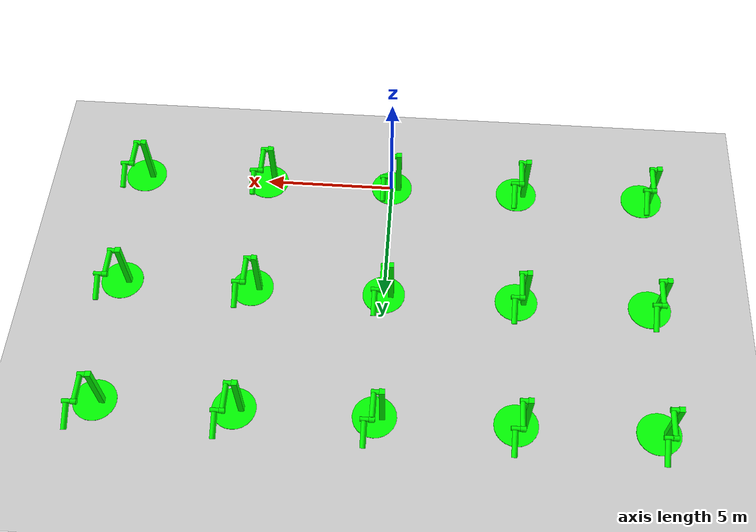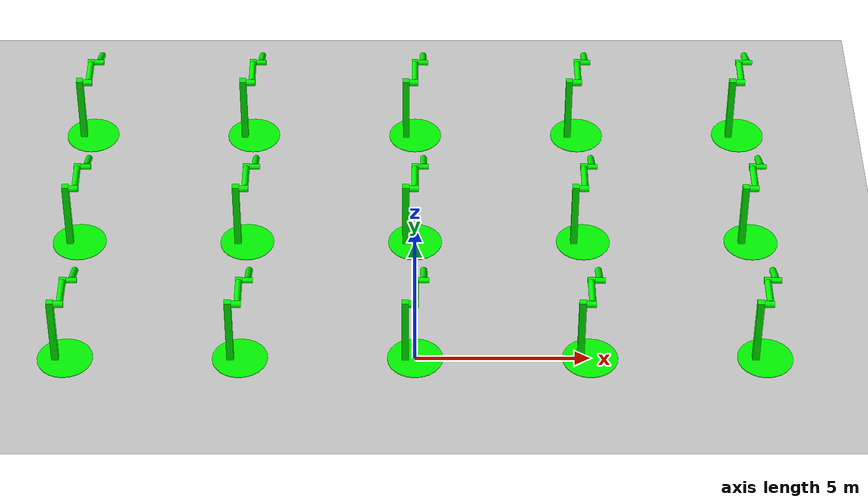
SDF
<?xml version="1.0" ?>
<!--
  to generate a world of 100 pendulums in a 10x10 grid,
  run `erb r=10 c=10 double_pendulums.sdf.erb > double_pendulums.sdf`
-->
<sdf version="1.6">
  <world name="double_pendulums">
    <model name="ground_plane">
      <static>true</static>
      <link name="link">
        <collision name="collision">
          <geometry>
            <plane>
              <normal>0 0 1</normal>
              <size>100 100</size>
            </plane>
          </geometry>
        </collision>
        <visual name="visual">
          <geometry>
            <plane>
              <normal>0 0 1</normal>
              <size>100 100</size>
            </plane>
          </geometry>
          <material>
            <ambient>0.8 0.8 0.8 1</ambient>
            <diffuse>0.8 0.8 0.8 1</diffuse>
            <specular>0.8 0.8 0.8 1</specular>
          </material>
        </visual>
      </link>
    </model>

    <model name="dbl_pendulum_0">
      <pose>-10 0 0 0 0 0</pose>
      <link name="base">
        <inertial>
          <mass>100</mass>
        </inertial>
        <visual name="vis_plate_on_ground">
          <pose>0 0 0.01 0 0 0</pose>
          <geometry>
            <cylinder>
              <radius>0.8</radius>
              <length>0.02</length>
            </cylinder>
          </geometry>
          <material>
            <ambient>0 1 0 1</ambient>
            <diffuse>0 1 0 1</diffuse>
            <specular>0 1 0 1</specular>
          </material>
        </visual>
        <visual name="vis_pole">
          <pose>-0.275 0 1.1 0 0 0</pose>
          <geometry>
            <box>
              <size>0.2 0.2 2.2</size>
            </box>
          </geometry>
          <material>
            <ambient>0 1 0 1</ambient>
            <diffuse>0 1 0 1</diffuse>
            <specular>0 1 0 1</specular>
          </material>
        </visual>
        <collision name="col_plate_on_ground">
          <pose>0 0 0.01 0 0 0</pose>
          <geometry>
            <cylinder>
              <radius>0.8</radius>
              <length>0.02</length>
            </cylinder>
          </geometry>
        </collision>
        <collision name="col_pole">
          <pose>-0.275 0 1.1 0 0 0</pose>
          <geometry>
            <box>
              <size>0.2 0.2 2.2</size>
            </box>
          </geometry>
        </collision>
      </link>
      <!-- upper link, length 1, IC -90 degrees -->
      <link name="upper_link">
        <pose>0 0 2.1 -1.5708 0 0</pose>
        <self_collide>0</self_collide>
        <inertial>
          <pose>0 0 0.5 0 0 0</pose>
        </inertial>
        <visual name="vis_upper_joint">
          <pose>-0.05 0 0 0 1.5708 0</pose>
          <geometry>
            <cylinder>
              <radius>0.1</radius>
              <length>0.3</length>
            </cylinder>
          </geometry>
          <material>
            <ambient>0 1 0 1</ambient>
            <diffuse>0 1 0 1</diffuse>
            <specular>0 1 0 1</specular>
          </material>
        </visual>
        <visual name="vis_lower_joint">
          <pose>0 0 1.0 0 1.5708 0</pose>
          <geometry>
            <cylinder>
              <radius>0.1</radius>
              <length>0.2</length>
            </cylinder>
          </geometry>
          <material>
            <ambient>0 1 0 1</ambient>
            <diffuse>0 1 0 1</diffuse>
            <specular>0 1 0 1</specular>
          </material>
        </visual>
        <visual name="vis_cylinder">
          <pose>0 0 0.5 0 0 0</pose>
          <geometry>
            <cylinder>
              <radius>0.1</radius>
              <length>0.9</length>
            </cylinder>
          </geometry>
          <material>
            <ambient>0 1 0 1</ambient>
            <diffuse>0 1 0 1</diffuse>
            <specular>0 1 0 1</specular>
          </material>
        </visual>
        <collision name="col_upper_joint">
          <pose>-0.05 0 0 0 1.5708 0</pose>
          <geometry>
            <cylinder>
              <radius>0.1</radius>
              <length>0.3</length>
            </cylinder>
          </geometry>
        </collision>
        <collision name="col_lower_joint">
          <pose>0 0 1.0 0 1.5708 0</pose>
          <geometry>
            <cylinder>
              <radius>0.1</radius>
              <length>0.2</length>
            </cylinder>
          </geometry>
        </collision>
        <collision name="col_cylinder">
          <pose>0 0 0.5 0 0 0</pose>
          <geometry>
            <cylinder>
              <radius>0.1</radius>
              <length>0.9</length>
            </cylinder>
          </geometry>
        </collision>
      </link>
      <!-- lower link, length 1, IC ~-120 degrees more -->
      <link name="lower_link">
        <pose>0.25 1.0 2.1 -2 0 0</pose>
        <self_collide>0</self_collide>
        <inertial>
          <pose>0 0 0.5 0 0 0</pose>
        </inertial>
        <visual name="vis_lower_joint">
          <pose>0 0 0 0 1.5708 0</pose>
          <geometry>
            <cylinder>
              <radius>0.08</radius>
              <length>0.3</length>
            </cylinder>
          </geometry>
          <material>
            <ambient>0 1 0 1</ambient>
            <diffuse>0 1 0 1</diffuse>
            <specular>0 1 0 1</specular>
          </material>
        </visual>
        <visual name="vis_cylinder">
          <pose>0 0 0.5 0 0 0</pose>
          <geometry>
            <cylinder>
              <radius>0.1</radius>
              <length>0.9</length>
            </cylinder>
          </geometry>
          <material>
            <ambient>0 1 0 1</ambient>
            <diffuse>0 1 0 1</diffuse>
            <specular>0 1 0 1</specular>
          </material>
        </visual>
        <collision name="col_lower_joint">
          <pose>0 0 0 0 1.5708 0</pose>
          <geometry>
            <cylinder>
              <radius>0.08</radius>
              <length>0.3</length>
            </cylinder>
          </geometry>
        </collision>
        <collision name="col_cylinder">
          <pose>0 0 0.5 0 0 0</pose>
          <geometry>
            <cylinder>
              <radius>0.1</radius>
              <length>0.9</length>
            </cylinder>
          </geometry>
        </collision>
      </link>
      <!-- pin joint for upper link, at origin of upper link -->
      <joint name="upper_joint" type="revolute">
        <parent>base</parent>
        <child>upper_link</child>
        <axis>
          <xyz>1.0 0 0</xyz>
        </axis>
      </joint>
      <!-- pin joint for lower link, at origin of child link -->
      <joint name="lower_joint" type="revolute">
        <parent>upper_link</parent>
        <child>lower_link</child>
        <axis>
          <xyz>1.0 0 0</xyz>
        </axis>
      </joint>
    </model>

    <model name="dbl_pendulum_1">
      <pose>-5 0 0 0 0 0</pose>
      <link name="base">
        <inertial>
          <mass>100</mass>
        </inertial>
        <visual name="vis_plate_on_ground">
          <pose>0 0 0.01 0 0 0</pose>
          <geometry>
            <cylinder>
              <radius>0.8</radius>
              <length>0.02</length>
            </cylinder>
          </geometry>
          <material>
            <ambient>0 1 0 1</ambient>
            <diffuse>0 1 0 1</diffuse>
            <specular>0 1 0 1</specular>
          </material>
        </visual>
        <visual name="vis_pole">
          <pose>-0.275 0 1.1 0 0 0</pose>
          <geometry>
            <box>
              <size>0.2 0.2 2.2</size>
            </box>
          </geometry>
          <material>
            <ambient>0 1 0 1</ambient>
            <diffuse>0 1 0 1</diffuse>
            <specular>0 1 0 1</specular>
          </material>
        </visual>
        <collision name="col_plate_on_ground">
          <pose>0 0 0.01 0 0 0</pose>
          <geometry>
            <cylinder>
              <radius>0.8</radius>
              <length>0.02</length>
            </cylinder>
          </geometry>
        </collision>
        <collision name="col_pole">
          <pose>-0.275 0 1.1 0 0 0</pose>
          <geometry>
            <box>
              <size>0.2 0.2 2.2</size>
            </box>
          </geometry>
        </collision>
      </link>
      <!-- upper link, length 1, IC -90 degrees -->
      <link name="upper_link">
        <pose>0 0 2.1 -1.5708 0 0</pose>
        <self_collide>0</self_collide>
        <inertial>
          <pose>0 0 0.5 0 0 0</pose>
        </inertial>
        <visual name="vis_upper_joint">
          <pose>-0.05 0 0 0 1.5708 0</pose>
          <geometry>
            <cylinder>
              <radius>0.1</radius>
              <length>0.3</length>
            </cylinder>
          </geometry>
          <material>
            <ambient>0 1 0 1</ambient>
            <diffuse>0 1 0 1</diffuse>
            <specular>0 1 0 1</specular>
          </material>
        </visual>
        <visual name="vis_lower_joint">
          <pose>0 0 1.0 0 1.5708 0</pose>
          <geometry>
            <cylinder>
              <radius>0.1</radius>
              <length>0.2</length>
            </cylinder>
          </geometry>
          <material>
            <ambient>0 1 0 1</ambient>
            <diffuse>0 1 0 1</diffuse>
            <specular>0 1 0 1</specular>
          </material>
        </visual>
        <visual name="vis_cylinder">
          <pose>0 0 0.5 0 0 0</pose>
          <geometry>
            <cylinder>
              <radius>0.1</radius>
              <length>0.9</length>
            </cylinder>
          </geometry>
          <material>
            <ambient>0 1 0 1</ambient>
            <diffuse>0 1 0 1</diffuse>
            <specular>0 1 0 1</specular>
          </material>
        </visual>
        <collision name="col_upper_joint">
          <pose>-0.05 0 0 0 1.5708 0</pose>
          <geometry>
            <cylinder>
              <radius>0.1</radius>
              <length>0.3</length>
            </cylinder>
          </geometry>
        </collision>
        <collision name="col_lower_joint">
          <pose>0 0 1.0 0 1.5708 0</pose>
          <geometry>
            <cylinder>
              <radius>0.1</radius>
              <length>0.2</length>
            </cylinder>
          </geometry>
        </collision>
        <collision name="col_cylinder">
          <pose>0 0 0.5 0 0 0</pose>
          <geometry>
            <cylinder>
              <radius>0.1</radius>
              <length>0.9</length>
            </cylinder>
          </geometry>
        </collision>
      </link>
      <!-- lower link, length 1, IC ~-120 degrees more -->
      <link name="lower_link">
        <pose>0.25 1.0 2.1 -2 0 0</pose>
        <self_collide>0</self_collide>
        <inertial>
          <pose>0 0 0.5 0 0 0</pose>
        </inertial>
        <visual name="vis_lower_joint">
          <pose>0 0 0 0 1.5708 0</pose>
          <geometry>
            <cylinder>
              <radius>0.08</radius>
              <length>0.3</length>
            </cylinder>
          </geometry>
          <material>
            <ambient>0 1 0 1</ambient>
            <diffuse>0 1 0 1</diffuse>
            <specular>0 1 0 1</specular>
          </material>
        </visual>
        <visual name="vis_cylinder">
          <pose>0 0 0.5 0 0 0</pose>
          <geometry>
            <cylinder>
              <radius>0.1</radius>
              <length>0.9</length>
            </cylinder>
          </geometry>
          <material>
            <ambient>0 1 0 1</ambient>
            <diffuse>0 1 0 1</diffuse>
            <specular>0 1 0 1</specular>
          </material>
        </visual>
        <collision name="col_lower_joint">
          <pose>0 0 0 0 1.5708 0</pose>
          <geometry>
            <cylinder>
              <radius>0.08</radius>
              <length>0.3</length>
            </cylinder>
          </geometry>
        </collision>
        <collision name="col_cylinder">
          <pose>0 0 0.5 0 0 0</pose>
          <geometry>
            <cylinder>
              <radius>0.1</radius>
              <length>0.9</length>
            </cylinder>
          </geometry>
        </collision>
      </link>
      <!-- pin joint for upper link, at origin of upper link -->
      <joint name="upper_joint" type="revolute">
        <parent>base</parent>
        <child>upper_link</child>
        <axis>
          <xyz>1.0 0 0</xyz>
        </axis>
      </joint>
      <!-- pin joint for lower link, at origin of child link -->
      <joint name="lower_joint" type="revolute">
        <parent>upper_link</parent>
        <child>lower_link</child>
        <axis>
          <xyz>1.0 0 0</xyz>
        </axis>
      </joint>
    </model>

    <model name="dbl_pendulum_2">
      <pose>0 0 0 0 0 0</pose>
      <link name="base">
        <inertial>
          <mass>100</mass>
        </inertial>
        <visual name="vis_plate_on_ground">
          <pose>0 0 0.01 0 0 0</pose>
          <geometry>
            <cylinder>
              <radius>0.8</radius>
              <length>0.02</length>
            </cylinder>
          </geometry>
          <material>
            <ambient>0 1 0 1</ambient>
            <diffuse>0 1 0 1</diffuse>
            <specular>0 1 0 1</specular>
          </material>
        </visual>
        <visual name="vis_pole">
          <pose>-0.275 0 1.1 0 0 0</pose>
          <geometry>
            <box>
              <size>0.2 0.2 2.2</size>
            </box>
          </geometry>
          <material>
            <ambient>0 1 0 1</ambient>
            <diffuse>0 1 0 1</diffuse>
            <specular>0 1 0 1</specular>
          </material>
        </visual>
        <collision name="col_plate_on_ground">
          <pose>0 0 0.01 0 0 0</pose>
          <geometry>
            <cylinder>
              <radius>0.8</radius>
              <length>0.02</length>
            </cylinder>
          </geometry>
        </collision>
        <collision name="col_pole">
          <pose>-0.275 0 1.1 0 0 0</pose>
          <geometry>
            <box>
              <size>0.2 0.2 2.2</size>
            </box>
          </geometry>
        </collision>
      </link>
      <!-- upper link, length 1, IC -90 degrees -->
      <link name="upper_link">
        <pose>0 0 2.1 -1.5708 0 0</pose>
        <self_collide>0</self_collide>
        <inertial>
          <pose>0 0 0.5 0 0 0</pose>
        </inertial>
        <visual name="vis_upper_joint">
          <pose>-0.05 0 0 0 1.5708 0</pose>
          <geometry>
            <cylinder>
              <radius>0.1</radius>
              <length>0.3</length>
            </cylinder>
          </geometry>
          <material>
            <ambient>0 1 0 1</ambient>
            <diffuse>0 1 0 1</diffuse>
            <specular>0 1 0 1</specular>
          </material>
        </visual>
        <visual name="vis_lower_joint">
          <pose>0 0 1.0 0 1.5708 0</pose>
          <geometry>
            <cylinder>
              <radius>0.1</radius>
              <length>0.2</length>
            </cylinder>
          </geometry>
          <material>
            <ambient>0 1 0 1</ambient>
            <diffuse>0 1 0 1</diffuse>
            <specular>0 1 0 1</specular>
          </material>
        </visual>
        <visual name="vis_cylinder">
          <pose>0 0 0.5 0 0 0</pose>
          <geometry>
            <cylinder>
              <radius>0.1</radius>
              <length>0.9</length>
            </cylinder>
          </geometry>
          <material>
            <ambient>0 1 0 1</ambient>
            <diffuse>0 1 0 1</diffuse>
            <specular>0 1 0 1</specular>
          </material>
        </visual>
        <collision name="col_upper_joint">
          <pose>-0.05 0 0 0 1.5708 0</pose>
          <geometry>
            <cylinder>
              <radius>0.1</radius>
              <length>0.3</length>
            </cylinder>
          </geometry>
        </collision>
        <collision name="col_lower_joint">
          <pose>0 0 1.0 0 1.5708 0</pose>
          <geometry>
            <cylinder>
              <radius>0.1</radius>
              <length>0.2</length>
            </cylinder>
          </geometry>
        </collision>
        <collision name="col_cylinder">
          <pose>0 0 0.5 0 0 0</pose>
          <geometry>
            <cylinder>
              <radius>0.1</radius>
              <length>0.9</length>
            </cylinder>
          </geometry>
        </collision>
      </link>
      <!-- lower link, length 1, IC ~-120 degrees more -->
      <link name="lower_link">
        <pose>0.25 1.0 2.1 -2 0 0</pose>
        <self_collide>0</self_collide>
        <inertial>
          <pose>0 0 0.5 0 0 0</pose>
        </inertial>
        <visual name="vis_lower_joint">
          <pose>0 0 0 0 1.5708 0</pose>
          <geometry>
            <cylinder>
              <radius>0.08</radius>
              <length>0.3</length>
            </cylinder>
          </geometry>
          <material>
            <ambient>0 1 0 1</ambient>
            <diffuse>0 1 0 1</diffuse>
            <specular>0 1 0 1</specular>
          </material>
        </visual>
        <visual name="vis_cylinder">
          <pose>0 0 0.5 0 0 0</pose>
          <geometry>
            <cylinder>
              <radius>0.1</radius>
              <length>0.9</length>
            </cylinder>
          </geometry>
          <material>
            <ambient>0 1 0 1</ambient>
            <diffuse>0 1 0 1</diffuse>
            <specular>0 1 0 1</specular>
          </material>
        </visual>
        <collision name="col_lower_joint">
          <pose>0 0 0 0 1.5708 0</pose>
          <geometry>
            <cylinder>
              <radius>0.08</radius>
              <length>0.3</length>
            </cylinder>
          </geometry>
        </collision>
        <collision name="col_cylinder">
          <pose>0 0 0.5 0 0 0</pose>
          <geometry>
            <cylinder>
              <radius>0.1</radius>
              <length>0.9</length>
            </cylinder>
          </geometry>
        </collision>
      </link>
      <!-- pin joint for upper link, at origin of upper link -->
      <joint name="upper_joint" type="revolute">
        <parent>base</parent>
        <child>upper_link</child>
        <axis>
          <xyz>1.0 0 0</xyz>
        </axis>
      </joint>
      <!-- pin joint for lower link, at origin of child link -->
      <joint name="lower_joint" type="revolute">
        <parent>upper_link</parent>
        <child>lower_link</child>
        <axis>
          <xyz>1.0 0 0</xyz>
        </axis>
      </joint>
    </model>

    <model name="dbl_pendulum_3">
      <pose>5 0 0 0 0 0</pose>
      <link name="base">
        <inertial>
          <mass>100</mass>
        </inertial>
        <visual name="vis_plate_on_ground">
          <pose>0 0 0.01 0 0 0</pose>
          <geometry>
            <cylinder>
              <radius>0.8</radius>
              <length>0.02</length>
            </cylinder>
          </geometry>
          <material>
            <ambient>0 1 0 1</ambient>
            <diffuse>0 1 0 1</diffuse>
            <specular>0 1 0 1</specular>
          </material>
        </visual>
        <visual name="vis_pole">
          <pose>-0.275 0 1.1 0 0 0</pose>
          <geometry>
            <box>
              <size>0.2 0.2 2.2</size>
            </box>
          </geometry>
          <material>
            <ambient>0 1 0 1</ambient>
            <diffuse>0 1 0 1</diffuse>
            <specular>0 1 0 1</specular>
          </material>
        </visual>
        <collision name="col_plate_on_ground">
          <pose>0 0 0.01 0 0 0</pose>
          <geometry>
            <cylinder>
              <radius>0.8</radius>
              <length>0.02</length>
            </cylinder>
          </geometry>
        </collision>
        <collision name="col_pole">
          <pose>-0.275 0 1.1 0 0 0</pose>
          <geometry>
            <box>
              <size>0.2 0.2 2.2</size>
            </box>
          </geometry>
        </collision>
      </link>
      <!-- upper link, length 1, IC -90 degrees -->
      <link name="upper_link">
        <pose>0 0 2.1 -1.5708 0 0</pose>
        <self_collide>0</self_collide>
        <inertial>
          <pose>0 0 0.5 0 0 0</pose>
        </inertial>
        <visual name="vis_upper_joint">
          <pose>-0.05 0 0 0 1.5708 0</pose>
          <geometry>
            <cylinder>
              <radius>0.1</radius>
              <length>0.3</length>
            </cylinder>
          </geometry>
          <material>
            <ambient>0 1 0 1</ambient>
            <diffuse>0 1 0 1</diffuse>
            <specular>0 1 0 1</specular>
          </material>
        </visual>
        <visual name="vis_lower_joint">
          <pose>0 0 1.0 0 1.5708 0</pose>
          <geometry>
            <cylinder>
              <radius>0.1</radius>
              <length>0.2</length>
            </cylinder>
          </geometry>
          <material>
            <ambient>0 1 0 1</ambient>
            <diffuse>0 1 0 1</diffuse>
            <specular>0 1 0 1</specular>
          </material>
        </visual>
        <visual name="vis_cylinder">
          <pose>0 0 0.5 0 0 0</pose>
          <geometry>
            <cylinder>
              <radius>0.1</radius>
              <length>0.9</length>
            </cylinder>
          </geometry>
          <material>
            <ambient>0 1 0 1</ambient>
            <diffuse>0 1 0 1</diffuse>
            <specular>0 1 0 1</specular>
          </material>
        </visual>
        <collision name="col_upper_joint">
          <pose>-0.05 0 0 0 1.5708 0</pose>
          <geometry>
            <cylinder>
              <radius>0.1</radius>
              <length>0.3</length>
            </cylinder>
          </geometry>
        </collision>
        <collision name="col_lower_joint">
          <pose>0 0 1.0 0 1.5708 0</pose>
          <geometry>
            <cylinder>
              <radius>0.1</radius>
              <length>0.2</length>
            </cylinder>
          </geometry>
        </collision>
        <collision name="col_cylinder">
          <pose>0 0 0.5 0 0 0</pose>
          <geometry>
            <cylinder>
              <radius>0.1</radius>
              <length>0.9</length>
            </cylinder>
          </geometry>
        </collision>
      </link>
      <!-- lower link, length 1, IC ~-120 degrees more -->
      <link name="lower_link">
        <pose>0.25 1.0 2.1 -2 0 0</pose>
        <self_collide>0</self_collide>
        <inertial>
          <pose>0 0 0.5 0 0 0</pose>
        </inertial>
        <visual name="vis_lower_joint">
          <pose>0 0 0 0 1.5708 0</pose>
          <geometry>
            <cylinder>
              <radius>0.08</radius>
              <length>0.3</length>
            </cylinder>
          </geometry>
          <material>
            <ambient>0 1 0 1</ambient>
            <diffuse>0 1 0 1</diffuse>
            <specular>0 1 0 1</specular>
          </material>
        </visual>
        <visual name="vis_cylinder">
          <pose>0 0 0.5 0 0 0</pose>
          <geometry>
            <cylinder>
              <radius>0.1</radius>
              <length>0.9</length>
            </cylinder>
          </geometry>
          <material>
            <ambient>0 1 0 1</ambient>
            <diffuse>0 1 0 1</diffuse>
            <specular>0 1 0 1</specular>
          </material>
        </visual>
        <collision name="col_lower_joint">
          <pose>0 0 0 0 1.5708 0</pose>
          <geometry>
            <cylinder>
              <radius>0.08</radius>
              <length>0.3</length>
            </cylinder>
          </geometry>
        </collision>
        <collision name="col_cylinder">
          <pose>0 0 0.5 0 0 0</pose>
          <geometry>
            <cylinder>
              <radius>0.1</radius>
              <length>0.9</length>
            </cylinder>
          </geometry>
        </collision>
      </link>
      <!-- pin joint for upper link, at origin of upper link -->
      <joint name="upper_joint" type="revolute">
        <parent>base</parent>
        <child>upper_link</child>
        <axis>
          <xyz>1.0 0 0</xyz>
        </axis>
      </joint>
      <!-- pin joint for lower link, at origin of child link -->
      <joint name="lower_joint" type="revolute">
        <parent>upper_link</parent>
        <child>lower_link</child>
        <axis>
          <xyz>1.0 0 0</xyz>
        </axis>
      </joint>
    </model>

    <model name="dbl_pendulum_4">
      <pose>10 0 0 0 0 0</pose>
      <link name="base">
        <inertial>
          <mass>100</mass>
        </inertial>
        <visual name="vis_plate_on_ground">
          <pose>0 0 0.01 0 0 0</pose>
          <geometry>
            <cylinder>
              <radius>0.8</radius>
              <length>0.02</length>
            </cylinder>
          </geometry>
          <material>
            <ambient>0 1 0 1</ambient>
            <diffuse>0 1 0 1</diffuse>
            <specular>0 1 0 1</specular>
          </material>
        </visual>
        <visual name="vis_pole">
          <pose>-0.275 0 1.1 0 0 0</pose>
          <geometry>
            <box>
              <size>0.2 0.2 2.2</size>
            </box>
          </geometry>
          <material>
            <ambient>0 1 0 1</ambient>
            <diffuse>0 1 0 1</diffuse>
            <specular>0 1 0 1</specular>
          </material>
        </visual>
        <collision name="col_plate_on_ground">
          <pose>0 0 0.01 0 0 0</pose>
          <geometry>
            <cylinder>
              <radius>0.8</radius>
              <length>0.02</length>
            </cylinder>
          </geometry>
        </collision>
        <collision name="col_pole">
          <pose>-0.275 0 1.1 0 0 0</pose>
          <geometry>
            <box>
              <size>0.2 0.2 2.2</size>
            </box>
          </geometry>
        </collision>
      </link>
      <!-- upper link, length 1, IC -90 degrees -->
      <link name="upper_link">
        <pose>0 0 2.1 -1.5708 0 0</pose>
        <self_collide>0</self_collide>
        <inertial>
          <pose>0 0 0.5 0 0 0</pose>
        </inertial>
        <visual name="vis_upper_joint">
          <pose>-0.05 0 0 0 1.5708 0</pose>
          <geometry>
            <cylinder>
              <radius>0.1</radius>
              <length>0.3</length>
            </cylinder>
          </geometry>
          <material>
            <ambient>0 1 0 1</ambient>
            <diffuse>0 1 0 1</diffuse>
            <specular>0 1 0 1</specular>
          </material>
        </visual>
        <visual name="vis_lower_joint">
          <pose>0 0 1.0 0 1.5708 0</pose>
          <geometry>
            <cylinder>
              <radius>0.1</radius>
              <length>0.2</length>
            </cylinder>
          </geometry>
          <material>
            <ambient>0 1 0 1</ambient>
            <diffuse>0 1 0 1</diffuse>
            <specular>0 1 0 1</specular>
          </material>
        </visual>
        <visual name="vis_cylinder">
          <pose>0 0 0.5 0 0 0</pose>
          <geometry>
            <cylinder>
              <radius>0.1</radius>
              <length>0.9</length>
            </cylinder>
          </geometry>
          <material>
            <ambient>0 1 0 1</ambient>
            <diffuse>0 1 0 1</diffuse>
            <specular>0 1 0 1</specular>
          </material>
        </visual>
        <collision name="col_upper_joint">
          <pose>-0.05 0 0 0 1.5708 0</pose>
          <geometry>
            <cylinder>
              <radius>0.1</radius>
              <length>0.3</length>
            </cylinder>
          </geometry>
        </collision>
        <collision name="col_lower_joint">
          <pose>0 0 1.0 0 1.5708 0</pose>
          <geometry>
            <cylinder>
              <radius>0.1</radius>
              <length>0.2</length>
            </cylinder>
          </geometry>
        </collision>
        <collision name="col_cylinder">
          <pose>0 0 0.5 0 0 0</pose>
          <geometry>
            <cylinder>
              <radius>0.1</radius>
              <length>0.9</length>
            </cylinder>
          </geometry>
        </collision>
      </link>
      <!-- lower link, length 1, IC ~-120 degrees more -->
      <link name="lower_link">
        <pose>0.25 1.0 2.1 -2 0 0</pose>
        <self_collide>0</self_collide>
        <inertial>
          <pose>0 0 0.5 0 0 0</pose>
        </inertial>
        <visual name="vis_lower_joint">
          <pose>0 0 0 0 1.5708 0</pose>
          <geometry>
            <cylinder>
              <radius>0.08</radius>
              <length>0.3</length>
            </cylinder>
          </geometry>
          <material>
            <ambient>0 1 0 1</ambient>
            <diffuse>0 1 0 1</diffuse>
            <specular>0 1 0 1</specular>
          </material>
        </visual>
        <visual name="vis_cylinder">
          <pose>0 0 0.5 0 0 0</pose>
          <geometry>
            <cylinder>
              <radius>0.1</radius>
              <length>0.9</length>
            </cylinder>
          </geometry>
          <material>
            <ambient>0 1 0 1</ambient>
            <diffuse>0 1 0 1</diffuse>
            <specular>0 1 0 1</specular>
          </material>
        </visual>
        <collision name="col_lower_joint">
          <pose>0 0 0 0 1.5708 0</pose>
          <geometry>
            <cylinder>
              <radius>0.08</radius>
              <length>0.3</length>
            </cylinder>
          </geometry>
        </collision>
        <collision name="col_cylinder">
          <pose>0 0 0.5 0 0 0</pose>
          <geometry>
            <cylinder>
              <radius>0.1</radius>
              <length>0.9</length>
            </cylinder>
          </geometry>
        </collision>
      </link>
      <!-- pin joint for upper link, at origin of upper link -->
      <joint name="upper_joint" type="revolute">
        <parent>base</parent>
        <child>upper_link</child>
        <axis>
          <xyz>1.0 0 0</xyz>
        </axis>
      </joint>
      <!-- pin joint for lower link, at origin of child link -->
      <joint name="lower_joint" type="revolute">
        <parent>upper_link</parent>
        <child>lower_link</child>
        <axis>
          <xyz>1.0 0 0</xyz>
        </axis>
      </joint>
    </model>

    <model name="dbl_pendulum_3">
      <pose>-10 5 0 0 0 0</pose>
      <link name="base">
        <inertial>
          <mass>100</mass>
        </inertial>
        <visual name="vis_plate_on_ground">
          <pose>0 0 0.01 0 0 0</pose>
          <geometry>
            <cylinder>
              <radius>0.8</radius>
              <length>0.02</length>
            </cylinder>
          </geometry>
          <material>
            <ambient>0 1 0 1</ambient>
            <diffuse>0 1 0 1</diffuse>
            <specular>0 1 0 1</specular>
          </material>
        </visual>
        <visual name="vis_pole">
          <pose>-0.275 0 1.1 0 0 0</pose>
          <geometry>
            <box>
              <size>0.2 0.2 2.2</size>
            </box>
          </geometry>
          <material>
            <ambient>0 1 0 1</ambient>
            <diffuse>0 1 0 1</diffuse>
            <specular>0 1 0 1</specular>
          </material>
        </visual>
        <collision name="col_plate_on_ground">
          <pose>0 0 0.01 0 0 0</pose>
          <geometry>
            <cylinder>
              <radius>0.8</radius>
              <length>0.02</length>
            </cylinder>
          </geometry>
        </collision>
        <collision name="col_pole">
          <pose>-0.275 0 1.1 0 0 0</pose>
          <geometry>
            <box>
              <size>0.2 0.2 2.2</size>
            </box>
          </geometry>
        </collision>
      </link>
      <!-- upper link, length 1, IC -90 degrees -->
      <link name="upper_link">
        <pose>0 0 2.1 -1.5708 0 0</pose>
        <self_collide>0</self_collide>
        <inertial>
          <pose>0 0 0.5 0 0 0</pose>
        </inertial>
        <visual name="vis_upper_joint">
          <pose>-0.05 0 0 0 1.5708 0</pose>
          <geometry>
            <cylinder>
              <radius>0.1</radius>
              <length>0.3</length>
            </cylinder>
          </geometry>
          <material>
            <ambient>0 1 0 1</ambient>
            <diffuse>0 1 0 1</diffuse>
            <specular>0 1 0 1</specular>
          </material>
        </visual>
        <visual name="vis_lower_joint">
          <pose>0 0 1.0 0 1.5708 0</pose>
          <geometry>
            <cylinder>
              <radius>0.1</radius>
              <length>0.2</length>
            </cylinder>
          </geometry>
          <material>
            <ambient>0 1 0 1</ambient>
            <diffuse>0 1 0 1</diffuse>
            <specular>0 1 0 1</specular>
          </material>
        </visual>
        <visual name="vis_cylinder">
          <pose>0 0 0.5 0 0 0</pose>
          <geometry>
            <cylinder>
              <radius>0.1</radius>
              <length>0.9</length>
            </cylinder>
          </geometry>
          <material>
            <ambient>0 1 0 1</ambient>
            <diffuse>0 1 0 1</diffuse>
            <specular>0 1 0 1</specular>
          </material>
        </visual>
        <collision name="col_upper_joint">
          <pose>-0.05 0 0 0 1.5708 0</pose>
          <geometry>
            <cylinder>
              <radius>0.1</radius>
              <length>0.3</length>
            </cylinder>
          </geometry>
        </collision>
        <collision name="col_lower_joint">
          <pose>0 0 1.0 0 1.5708 0</pose>
          <geometry>
            <cylinder>
              <radius>0.1</radius>
              <length>0.2</length>
            </cylinder>
          </geometry>
        </collision>
        <collision name="col_cylinder">
          <pose>0 0 0.5 0 0 0</pose>
          <geometry>
            <cylinder>
              <radius>0.1</radius>
              <length>0.9</length>
            </cylinder>
          </geometry>
        </collision>
      </link>
      <!-- lower link, length 1, IC ~-120 degrees more -->
      <link name="lower_link">
        <pose>0.25 1.0 2.1 -2 0 0</pose>
        <self_collide>0</self_collide>
        <inertial>
          <pose>0 0 0.5 0 0 0</pose>
        </inertial>
        <visual name="vis_lower_joint">
          <pose>0 0 0 0 1.5708 0</pose>
          <geometry>
            <cylinder>
              <radius>0.08</radius>
              <length>0.3</length>
            </cylinder>
          </geometry>
          <material>
            <ambient>0 1 0 1</ambient>
            <diffuse>0 1 0 1</diffuse>
            <specular>0 1 0 1</specular>
          </material>
        </visual>
        <visual name="vis_cylinder">
          <pose>0 0 0.5 0 0 0</pose>
          <geometry>
            <cylinder>
              <radius>0.1</radius>
              <length>0.9</length>
            </cylinder>
          </geometry>
          <material>
            <ambient>0 1 0 1</ambient>
            <diffuse>0 1 0 1</diffuse>
            <specular>0 1 0 1</specular>
          </material>
        </visual>
        <collision name="col_lower_joint">
          <pose>0 0 0 0 1.5708 0</pose>
          <geometry>
            <cylinder>
              <radius>0.08</radius>
              <length>0.3</length>
            </cylinder>
          </geometry>
        </collision>
        <collision name="col_cylinder">
          <pose>0 0 0.5 0 0 0</pose>
          <geometry>
            <cylinder>
              <radius>0.1</radius>
              <length>0.9</length>
            </cylinder>
          </geometry>
        </collision>
      </link>
      <!-- pin joint for upper link, at origin of upper link -->
      <joint name="upper_joint" type="revolute">
        <parent>base</parent>
        <child>upper_link</child>
        <axis>
          <xyz>1.0 0 0</xyz>
        </axis>
      </joint>
      <!-- pin joint for lower link, at origin of child link -->
      <joint name="lower_joint" type="revolute">
        <parent>upper_link</parent>
        <child>lower_link</child>
        <axis>
          <xyz>1.0 0 0</xyz>
        </axis>
      </joint>
    </model>

    <model name="dbl_pendulum_4">
      <pose>-5 5 0 0 0 0</pose>
      <link name="base">
        <inertial>
          <mass>100</mass>
        </inertial>
        <visual name="vis_plate_on_ground">
          <pose>0 0 0.01 0 0 0</pose>
          <geometry>
            <cylinder>
              <radius>0.8</radius>
              <length>0.02</length>
            </cylinder>
          </geometry>
          <material>
            <ambient>0 1 0 1</ambient>
            <diffuse>0 1 0 1</diffuse>
            <specular>0 1 0 1</specular>
          </material>
        </visual>
        <visual name="vis_pole">
          <pose>-0.275 0 1.1 0 0 0</pose>
          <geometry>
            <box>
              <size>0.2 0.2 2.2</size>
            </box>
          </geometry>
          <material>
            <ambient>0 1 0 1</ambient>
            <diffuse>0 1 0 1</diffuse>
            <specular>0 1 0 1</specular>
          </material>
        </visual>
        <collision name="col_plate_on_ground">
          <pose>0 0 0.01 0 0 0</pose>
          <geometry>
            <cylinder>
              <radius>0.8</radius>
              <length>0.02</length>
            </cylinder>
          </geometry>
        </collision>
        <collision name="col_pole">
          <pose>-0.275 0 1.1 0 0 0</pose>
          <geometry>
            <box>
              <size>0.2 0.2 2.2</size>
            </box>
          </geometry>
        </collision>
      </link>
      <!-- upper link, length 1, IC -90 degrees -->
      <link name="upper_link">
        <pose>0 0 2.1 -1.5708 0 0</pose>
        <self_collide>0</self_collide>
        <inertial>
          <pose>0 0 0.5 0 0 0</pose>
        </inertial>
        <visual name="vis_upper_joint">
          <pose>-0.05 0 0 0 1.5708 0</pose>
          <geometry>
            <cylinder>
              <radius>0.1</radius>
              <length>0.3</length>
            </cylinder>
          </geometry>
          <material>
            <ambient>0 1 0 1</ambient>
            <diffuse>0 1 0 1</diffuse>
            <specular>0 1 0 1</specular>
          </material>
        </visual>
        <visual name="vis_lower_joint">
          <pose>0 0 1.0 0 1.5708 0</pose>
          <geometry>
            <cylinder>
              <radius>0.1</radius>
              <length>0.2</length>
            </cylinder>
          </geometry>
          <material>
            <ambient>0 1 0 1</ambient>
            <diffuse>0 1 0 1</diffuse>
            <specular>0 1 0 1</specular>
          </material>
        </visual>
        <visual name="vis_cylinder">
          <pose>0 0 0.5 0 0 0</pose>
          <geometry>
            <cylinder>
              <radius>0.1</radius>
              <length>0.9</length>
            </cylinder>
          </geometry>
          <material>
            <ambient>0 1 0 1</ambient>
            <diffuse>0 1 0 1</diffuse>
            <specular>0 1 0 1</specular>
          </material>
        </visual>
        <collision name="col_upper_joint">
          <pose>-0.05 0 0 0 1.5708 0</pose>
          <geometry>
            <cylinder>
              <radius>0.1</radius>
              <length>0.3</length>
            </cylinder>
          </geometry>
        </collision>
        <collision name="col_lower_joint">
          <pose>0 0 1.0 0 1.5708 0</pose>
          <geometry>
            <cylinder>
              <radius>0.1</radius>
              <length>0.2</length>
            </cylinder>
          </geometry>
        </collision>
        <collision name="col_cylinder">
          <pose>0 0 0.5 0 0 0</pose>
          <geometry>
            <cylinder>
              <radius>0.1</radius>
              <length>0.9</length>
            </cylinder>
          </geometry>
        </collision>
      </link>
      <!-- lower link, length 1, IC ~-120 degrees more -->
      <link name="lower_link">
        <pose>0.25 1.0 2.1 -2 0 0</pose>
        <self_collide>0</self_collide>
        <inertial>
          <pose>0 0 0.5 0 0 0</pose>
        </inertial>
        <visual name="vis_lower_joint">
          <pose>0 0 0 0 1.5708 0</pose>
          <geometry>
            <cylinder>
              <radius>0.08</radius>
              <length>0.3</length>
            </cylinder>
          </geometry>
          <material>
            <ambient>0 1 0 1</ambient>
            <diffuse>0 1 0 1</diffuse>
            <specular>0 1 0 1</specular>
          </material>
        </visual>
        <visual name="vis_cylinder">
          <pose>0 0 0.5 0 0 0</pose>
          <geometry>
            <cylinder>
              <radius>0.1</radius>
              <length>0.9</length>
            </cylinder>
          </geometry>
          <material>
            <ambient>0 1 0 1</ambient>
            <diffuse>0 1 0 1</diffuse>
            <specular>0 1 0 1</specular>
          </material>
        </visual>
        <collision name="col_lower_joint">
          <pose>0 0 0 0 1.5708 0</pose>
          <geometry>
            <cylinder>
              <radius>0.08</radius>
              <length>0.3</length>
            </cylinder>
          </geometry>
        </collision>
        <collision name="col_cylinder">
          <pose>0 0 0.5 0 0 0</pose>
          <geometry>
            <cylinder>
              <radius>0.1</radius>
              <length>0.9</length>
            </cylinder>
          </geometry>
        </collision>
      </link>
      <!-- pin joint for upper link, at origin of upper link -->
      <joint name="upper_joint" type="revolute">
        <parent>base</parent>
        <child>upper_link</child>
        <axis>
          <xyz>1.0 0 0</xyz>
        </axis>
      </joint>
      <!-- pin joint for lower link, at origin of child link -->
      <joint name="lower_joint" type="revolute">
        <parent>upper_link</parent>
        <child>lower_link</child>
        <axis>
          <xyz>1.0 0 0</xyz>
        </axis>
      </joint>
    </model>

    <model name="dbl_pendulum_5">
      <pose>0 5 0 0 0 0</pose>
      <link name="base">
        <inertial>
          <mass>100</mass>
        </inertial>
        <visual name="vis_plate_on_ground">
          <pose>0 0 0.01 0 0 0</pose>
          <geometry>
            <cylinder>
              <radius>0.8</radius>
              <length>0.02</length>
            </cylinder>
          </geometry>
          <material>
            <ambient>0 1 0 1</ambient>
            <diffuse>0 1 0 1</diffuse>
            <specular>0 1 0 1</specular>
          </material>
        </visual>
        <visual name="vis_pole">
          <pose>-0.275 0 1.1 0 0 0</pose>
          <geometry>
            <box>
              <size>0.2 0.2 2.2</size>
            </box>
          </geometry>
          <material>
            <ambient>0 1 0 1</ambient>
            <diffuse>0 1 0 1</diffuse>
            <specular>0 1 0 1</specular>
          </material>
        </visual>
        <collision name="col_plate_on_ground">
          <pose>0 0 0.01 0 0 0</pose>
          <geometry>
            <cylinder>
              <radius>0.8</radius>
              <length>0.02</length>
            </cylinder>
          </geometry>
        </collision>
        <collision name="col_pole">
          <pose>-0.275 0 1.1 0 0 0</pose>
          <geometry>
            <box>
              <size>0.2 0.2 2.2</size>
            </box>
          </geometry>
        </collision>
      </link>
      <!-- upper link, length 1, IC -90 degrees -->
      <link name="upper_link">
        <pose>0 0 2.1 -1.5708 0 0</pose>
        <self_collide>0</self_collide>
        <inertial>
          <pose>0 0 0.5 0 0 0</pose>
        </inertial>
        <visual name="vis_upper_joint">
          <pose>-0.05 0 0 0 1.5708 0</pose>
          <geometry>
            <cylinder>
              <radius>0.1</radius>
              <length>0.3</length>
            </cylinder>
          </geometry>
          <material>
            <ambient>0 1 0 1</ambient>
            <diffuse>0 1 0 1</diffuse>
            <specular>0 1 0 1</specular>
          </material>
        </visual>
        <visual name="vis_lower_joint">
          <pose>0 0 1.0 0 1.5708 0</pose>
          <geometry>
            <cylinder>
              <radius>0.1</radius>
              <length>0.2</length>
            </cylinder>
          </geometry>
          <material>
            <ambient>0 1 0 1</ambient>
            <diffuse>0 1 0 1</diffuse>
            <specular>0 1 0 1</specular>
          </material>
        </visual>
        <visual name="vis_cylinder">
          <pose>0 0 0.5 0 0 0</pose>
          <geometry>
            <cylinder>
              <radius>0.1</radius>
              <length>0.9</length>
            </cylinder>
          </geometry>
          <material>
            <ambient>0 1 0 1</ambient>
            <diffuse>0 1 0 1</diffuse>
            <specular>0 1 0 1</specular>
          </material>
        </visual>
        <collision name="col_upper_joint">
          <pose>-0.05 0 0 0 1.5708 0</pose>
          <geometry>
            <cylinder>
              <radius>0.1</radius>
              <length>0.3</length>
            </cylinder>
          </geometry>
        </collision>
        <collision name="col_lower_joint">
          <pose>0 0 1.0 0 1.5708 0</pose>
          <geometry>
            <cylinder>
              <radius>0.1</radius>
              <length>0.2</length>
            </cylinder>
          </geometry>
        </collision>
        <collision name="col_cylinder">
          <pose>0 0 0.5 0 0 0</pose>
          <geometry>
            <cylinder>
              <radius>0.1</radius>
              <length>0.9</length>
            </cylinder>
          </geometry>
        </collision>
      </link>
      <!-- lower link, length 1, IC ~-120 degrees more -->
      <link name="lower_link">
        <pose>0.25 1.0 2.1 -2 0 0</pose>
        <self_collide>0</self_collide>
        <inertial>
          <pose>0 0 0.5 0 0 0</pose>
        </inertial>
        <visual name="vis_lower_joint">
          <pose>0 0 0 0 1.5708 0</pose>
          <geometry>
            <cylinder>
              <radius>0.08</radius>
              <length>0.3</length>
            </cylinder>
          </geometry>
          <material>
            <ambient>0 1 0 1</ambient>
            <diffuse>0 1 0 1</diffuse>
            <specular>0 1 0 1</specular>
          </material>
        </visual>
        <visual name="vis_cylinder">
          <pose>0 0 0.5 0 0 0</pose>
          <geometry>
            <cylinder>
              <radius>0.1</radius>
              <length>0.9</length>
            </cylinder>
          </geometry>
          <material>
            <ambient>0 1 0 1</ambient>
            <diffuse>0 1 0 1</diffuse>
            <specular>0 1 0 1</specular>
          </material>
        </visual>
        <collision name="col_lower_joint">
          <pose>0 0 0 0 1.5708 0</pose>
          <geometry>
            <cylinder>
              <radius>0.08</radius>
              <length>0.3</length>
            </cylinder>
          </geometry>
        </collision>
        <collision name="col_cylinder">
          <pose>0 0 0.5 0 0 0</pose>
          <geometry>
            <cylinder>
              <radius>0.1</radius>
              <length>0.9</length>
            </cylinder>
          </geometry>
        </collision>
      </link>
      <!-- pin joint for upper link, at origin of upper link -->
      <joint name="upper_joint" type="revolute">
        <parent>base</parent>
        <child>upper_link</child>
        <axis>
          <xyz>1.0 0 0</xyz>
        </axis>
      </joint>
      <!-- pin joint for lower link, at origin of child link -->
      <joint name="lower_joint" type="revolute">
        <parent>upper_link</parent>
        <child>lower_link</child>
        <axis>
          <xyz>1.0 0 0</xyz>
        </axis>
      </joint>
    </model>

    <model name="dbl_pendulum_6">
      <pose>5 5 0 0 0 0</pose>
      <link name="base">
        <inertial>
          <mass>100</mass>
        </inertial>
        <visual name="vis_plate_on_ground">
          <pose>0 0 0.01 0 0 0</pose>
          <geometry>
            <cylinder>
              <radius>0.8</radius>
              <length>0.02</length>
            </cylinder>
          </geometry>
          <material>
            <ambient>0 1 0 1</ambient>
            <diffuse>0 1 0 1</diffuse>
            <specular>0 1 0 1</specular>
          </material>
        </visual>
        <visual name="vis_pole">
          <pose>-0.275 0 1.1 0 0 0</pose>
          <geometry>
            <box>
              <size>0.2 0.2 2.2</size>
            </box>
          </geometry>
          <material>
            <ambient>0 1 0 1</ambient>
            <diffuse>0 1 0 1</diffuse>
            <specular>0 1 0 1</specular>
          </material>
        </visual>
        <collision name="col_plate_on_ground">
          <pose>0 0 0.01 0 0 0</pose>
          <geometry>
            <cylinder>
              <radius>0.8</radius>
              <length>0.02</length>
            </cylinder>
          </geometry>
        </collision>
        <collision name="col_pole">
          <pose>-0.275 0 1.1 0 0 0</pose>
          <geometry>
            <box>
              <size>0.2 0.2 2.2</size>
            </box>
          </geometry>
        </collision>
      </link>
      <!-- upper link, length 1, IC -90 degrees -->
      <link name="upper_link">
        <pose>0 0 2.1 -1.5708 0 0</pose>
        <self_collide>0</self_collide>
        <inertial>
          <pose>0 0 0.5 0 0 0</pose>
        </inertial>
        <visual name="vis_upper_joint">
          <pose>-0.05 0 0 0 1.5708 0</pose>
          <geometry>
            <cylinder>
              <radius>0.1</radius>
              <length>0.3</length>
            </cylinder>
          </geometry>
          <material>
            <ambient>0 1 0 1</ambient>
            <diffuse>0 1 0 1</diffuse>
            <specular>0 1 0 1</specular>
          </material>
        </visual>
        <visual name="vis_lower_joint">
          <pose>0 0 1.0 0 1.5708 0</pose>
          <geometry>
            <cylinder>
              <radius>0.1</radius>
              <length>0.2</length>
            </cylinder>
          </geometry>
          <material>
            <ambient>0 1 0 1</ambient>
            <diffuse>0 1 0 1</diffuse>
            <specular>0 1 0 1</specular>
          </material>
        </visual>
        <visual name="vis_cylinder">
          <pose>0 0 0.5 0 0 0</pose>
          <geometry>
            <cylinder>
              <radius>0.1</radius>
              <length>0.9</length>
            </cylinder>
          </geometry>
          <material>
            <ambient>0 1 0 1</ambient>
            <diffuse>0 1 0 1</diffuse>
            <specular>0 1 0 1</specular>
          </material>
        </visual>
        <collision name="col_upper_joint">
          <pose>-0.05 0 0 0 1.5708 0</pose>
          <geometry>
            <cylinder>
              <radius>0.1</radius>
              <length>0.3</length>
            </cylinder>
          </geometry>
        </collision>
        <collision name="col_lower_joint">
          <pose>0 0 1.0 0 1.5708 0</pose>
          <geometry>
            <cylinder>
              <radius>0.1</radius>
              <length>0.2</length>
            </cylinder>
          </geometry>
        </collision>
        <collision name="col_cylinder">
          <pose>0 0 0.5 0 0 0</pose>
          <geometry>
            <cylinder>
              <radius>0.1</radius>
              <length>0.9</length>
            </cylinder>
          </geometry>
        </collision>
      </link>
      <!-- lower link, length 1, IC ~-120 degrees more -->
      <link name="lower_link">
        <pose>0.25 1.0 2.1 -2 0 0</pose>
        <self_collide>0</self_collide>
        <inertial>
          <pose>0 0 0.5 0 0 0</pose>
        </inertial>
        <visual name="vis_lower_joint">
          <pose>0 0 0 0 1.5708 0</pose>
          <geometry>
            <cylinder>
              <radius>0.08</radius>
              <length>0.3</length>
            </cylinder>
          </geometry>
          <material>
            <ambient>0 1 0 1</ambient>
            <diffuse>0 1 0 1</diffuse>
            <specular>0 1 0 1</specular>
          </material>
        </visual>
        <visual name="vis_cylinder">
          <pose>0 0 0.5 0 0 0</pose>
          <geometry>
            <cylinder>
              <radius>0.1</radius>
              <length>0.9</length>
            </cylinder>
          </geometry>
          <material>
            <ambient>0 1 0 1</ambient>
            <diffuse>0 1 0 1</diffuse>
            <specular>0 1 0 1</specular>
          </material>
        </visual>
        <collision name="col_lower_joint">
          <pose>0 0 0 0 1.5708 0</pose>
          <geometry>
            <cylinder>
              <radius>0.08</radius>
              <length>0.3</length>
            </cylinder>
          </geometry>
        </collision>
        <collision name="col_cylinder">
          <pose>0 0 0.5 0 0 0</pose>
          <geometry>
            <cylinder>
              <radius>0.1</radius>
              <length>0.9</length>
            </cylinder>
          </geometry>
        </collision>
      </link>
      <!-- pin joint for upper link, at origin of upper link -->
      <joint name="upper_joint" type="revolute">
        <parent>base</parent>
        <child>upper_link</child>
        <axis>
          <xyz>1.0 0 0</xyz>
        </axis>
      </joint>
      <!-- pin joint for lower link, at origin of child link -->
      <joint name="lower_joint" type="revolute">
        <parent>upper_link</parent>
        <child>lower_link</child>
        <axis>
          <xyz>1.0 0 0</xyz>
        </axis>
      </joint>
    </model>

    <model name="dbl_pendulum_7">
      <pose>10 5 0 0 0 0</pose>
      <link name="base">
        <inertial>
          <mass>100</mass>
        </inertial>
        <visual name="vis_plate_on_ground">
          <pose>0 0 0.01 0 0 0</pose>
          <geometry>
            <cylinder>
              <radius>0.8</radius>
              <length>0.02</length>
            </cylinder>
          </geometry>
          <material>
            <ambient>0 1 0 1</ambient>
            <diffuse>0 1 0 1</diffuse>
            <specular>0 1 0 1</specular>
          </material>
        </visual>
        <visual name="vis_pole">
          <pose>-0.275 0 1.1 0 0 0</pose>
          <geometry>
            <box>
              <size>0.2 0.2 2.2</size>
            </box>
          </geometry>
          <material>
            <ambient>0 1 0 1</ambient>
            <diffuse>0 1 0 1</diffuse>
            <specular>0 1 0 1</specular>
          </material>
        </visual>
        <collision name="col_plate_on_ground">
          <pose>0 0 0.01 0 0 0</pose>
          <geometry>
            <cylinder>
              <radius>0.8</radius>
              <length>0.02</length>
            </cylinder>
          </geometry>
        </collision>
        <collision name="col_pole">
          <pose>-0.275 0 1.1 0 0 0</pose>
          <geometry>
            <box>
              <size>0.2 0.2 2.2</size>
            </box>
          </geometry>
        </collision>
      </link>
      <!-- upper link, length 1, IC -90 degrees -->
      <link name="upper_link">
        <pose>0 0 2.1 -1.5708 0 0</pose>
        <self_collide>0</self_collide>
        <inertial>
          <pose>0 0 0.5 0 0 0</pose>
        </inertial>
        <visual name="vis_upper_joint">
          <pose>-0.05 0 0 0 1.5708 0</pose>
          <geometry>
            <cylinder>
              <radius>0.1</radius>
              <length>0.3</length>
            </cylinder>
          </geometry>
          <material>
            <ambient>0 1 0 1</ambient>
            <diffuse>0 1 0 1</diffuse>
            <specular>0 1 0 1</specular>
          </material>
        </visual>
        <visual name="vis_lower_joint">
          <pose>0 0 1.0 0 1.5708 0</pose>
          <geometry>
            <cylinder>
              <radius>0.1</radius>
              <length>0.2</length>
            </cylinder>
          </geometry>
          <material>
            <ambient>0 1 0 1</ambient>
            <diffuse>0 1 0 1</diffuse>
            <specular>0 1 0 1</specular>
          </material>
        </visual>
        <visual name="vis_cylinder">
          <pose>0 0 0.5 0 0 0</pose>
          <geometry>
            <cylinder>
              <radius>0.1</radius>
              <length>0.9</length>
            </cylinder>
          </geometry>
          <material>
            <ambient>0 1 0 1</ambient>
            <diffuse>0 1 0 1</diffuse>
            <specular>0 1 0 1</specular>
          </material>
        </visual>
        <collision name="col_upper_joint">
          <pose>-0.05 0 0 0 1.5708 0</pose>
          <geometry>
            <cylinder>
              <radius>0.1</radius>
              <length>0.3</length>
            </cylinder>
          </geometry>
        </collision>
        <collision name="col_lower_joint">
          <pose>0 0 1.0 0 1.5708 0</pose>
          <geometry>
            <cylinder>
              <radius>0.1</radius>
              <length>0.2</length>
            </cylinder>
          </geometry>
        </collision>
        <collision name="col_cylinder">
          <pose>0 0 0.5 0 0 0</pose>
          <geometry>
            <cylinder>
              <radius>0.1</radius>
              <length>0.9</length>
            </cylinder>
          </geometry>
        </collision>
      </link>
      <!-- lower link, length 1, IC ~-120 degrees more -->
      <link name="lower_link">
        <pose>0.25 1.0 2.1 -2 0 0</pose>
        <self_collide>0</self_collide>
        <inertial>
          <pose>0 0 0.5 0 0 0</pose>
        </inertial>
        <visual name="vis_lower_joint">
          <pose>0 0 0 0 1.5708 0</pose>
          <geometry>
            <cylinder>
              <radius>0.08</radius>
              <length>0.3</length>
            </cylinder>
          </geometry>
          <material>
            <ambient>0 1 0 1</ambient>
            <diffuse>0 1 0 1</diffuse>
            <specular>0 1 0 1</specular>
          </material>
        </visual>
        <visual name="vis_cylinder">
          <pose>0 0 0.5 0 0 0</pose>
          <geometry>
            <cylinder>
              <radius>0.1</radius>
              <length>0.9</length>
            </cylinder>
          </geometry>
          <material>
            <ambient>0 1 0 1</ambient>
            <diffuse>0 1 0 1</diffuse>
            <specular>0 1 0 1</specular>
          </material>
        </visual>
        <collision name="col_lower_joint">
          <pose>0 0 0 0 1.5708 0</pose>
          <geometry>
            <cylinder>
              <radius>0.08</radius>
              <length>0.3</length>
            </cylinder>
          </geometry>
        </collision>
        <collision name="col_cylinder">
          <pose>0 0 0.5 0 0 0</pose>
          <geometry>
            <cylinder>
              <radius>0.1</radius>
              <length>0.9</length>
            </cylinder>
          </geometry>
        </collision>
      </link>
      <!-- pin joint for upper link, at origin of upper link -->
      <joint name="upper_joint" type="revolute">
        <parent>base</parent>
        <child>upper_link</child>
        <axis>
          <xyz>1.0 0 0</xyz>
        </axis>
      </joint>
      <!-- pin joint for lower link, at origin of child link -->
      <joint name="lower_joint" type="revolute">
        <parent>upper_link</parent>
        <child>lower_link</child>
        <axis>
          <xyz>1.0 0 0</xyz>
        </axis>
      </joint>
    </model>

    <model name="dbl_pendulum_6">
      <pose>-10 10 0 0 0 0</pose>
      <link name="base">
        <inertial>
          <mass>100</mass>
        </inertial>
        <visual name="vis_plate_on_ground">
          <pose>0 0 0.01 0 0 0</pose>
          <geometry>
            <cylinder>
              <radius>0.8</radius>
              <length>0.02</length>
            </cylinder>
          </geometry>
          <material>
            <ambient>0 1 0 1</ambient>
            <diffuse>0 1 0 1</diffuse>
            <specular>0 1 0 1</specular>
          </material>
        </visual>
        <visual name="vis_pole">
          <pose>-0.275 0 1.1 0 0 0</pose>
          <geometry>
            <box>
              <size>0.2 0.2 2.2</size>
            </box>
          </geometry>
          <material>
            <ambient>0 1 0 1</ambient>
            <diffuse>0 1 0 1</diffuse>
            <specular>0 1 0 1</specular>
          </material>
        </visual>
        <collision name="col_plate_on_ground">
          <pose>0 0 0.01 0 0 0</pose>
          <geometry>
            <cylinder>
              <radius>0.8</radius>
              <length>0.02</length>
            </cylinder>
          </geometry>
        </collision>
        <collision name="col_pole">
          <pose>-0.275 0 1.1 0 0 0</pose>
          <geometry>
            <box>
              <size>0.2 0.2 2.2</size>
            </box>
          </geometry>
        </collision>
      </link>
      <!-- upper link, length 1, IC -90 degrees -->
      <link name="upper_link">
        <pose>0 0 2.1 -1.5708 0 0</pose>
        <self_collide>0</self_collide>
        <inertial>
          <pose>0 0 0.5 0 0 0</pose>
        </inertial>
        <visual name="vis_upper_joint">
          <pose>-0.05 0 0 0 1.5708 0</pose>
          <geometry>
            <cylinder>
              <radius>0.1</radius>
              <length>0.3</length>
            </cylinder>
          </geometry>
          <material>
            <ambient>0 1 0 1</ambient>
            <diffuse>0 1 0 1</diffuse>
            <specular>0 1 0 1</specular>
          </material>
        </visual>
        <visual name="vis_lower_joint">
          <pose>0 0 1.0 0 1.5708 0</pose>
          <geometry>
            <cylinder>
              <radius>0.1</radius>
              <length>0.2</length>
            </cylinder>
          </geometry>
          <material>
            <ambient>0 1 0 1</ambient>
            <diffuse>0 1 0 1</diffuse>
            <specular>0 1 0 1</specular>
          </material>
        </visual>
        <visual name="vis_cylinder">
          <pose>0 0 0.5 0 0 0</pose>
          <geometry>
            <cylinder>
              <radius>0.1</radius>
              <length>0.9</length>
            </cylinder>
          </geometry>
          <material>
            <ambient>0 1 0 1</ambient>
            <diffuse>0 1 0 1</diffuse>
            <specular>0 1 0 1</specular>
          </material>
        </visual>
        <collision name="col_upper_joint">
          <pose>-0.05 0 0 0 1.5708 0</pose>
          <geometry>
            <cylinder>
              <radius>0.1</radius>
              <length>0.3</length>
            </cylinder>
          </geometry>
        </collision>
        <collision name="col_lower_joint">
          <pose>0 0 1.0 0 1.5708 0</pose>
          <geometry>
            <cylinder>
              <radius>0.1</radius>
              <length>0.2</length>
            </cylinder>
          </geometry>
        </collision>
        <collision name="col_cylinder">
          <pose>0 0 0.5 0 0 0</pose>
          <geometry>
            <cylinder>
              <radius>0.1</radius>
              <length>0.9</length>
            </cylinder>
          </geometry>
        </collision>
      </link>
      <!-- lower link, length 1, IC ~-120 degrees more -->
      <link name="lower_link">
        <pose>0.25 1.0 2.1 -2 0 0</pose>
        <self_collide>0</self_collide>
        <inertial>
          <pose>0 0 0.5 0 0 0</pose>
        </inertial>
        <visual name="vis_lower_joint">
          <pose>0 0 0 0 1.5708 0</pose>
          <geometry>
            <cylinder>
              <radius>0.08</radius>
              <length>0.3</length>
            </cylinder>
          </geometry>
          <material>
            <ambient>0 1 0 1</ambient>
            <diffuse>0 1 0 1</diffuse>
            <specular>0 1 0 1</specular>
          </material>
        </visual>
        <visual name="vis_cylinder">
          <pose>0 0 0.5 0 0 0</pose>
          <geometry>
            <cylinder>
              <radius>0.1</radius>
              <length>0.9</length>
            </cylinder>
          </geometry>
          <material>
            <ambient>0 1 0 1</ambient>
            <diffuse>0 1 0 1</diffuse>
            <specular>0 1 0 1</specular>
          </material>
        </visual>
        <collision name="col_lower_joint">
          <pose>0 0 0 0 1.5708 0</pose>
          <geometry>
            <cylinder>
              <radius>0.08</radius>
              <length>0.3</length>
            </cylinder>
          </geometry>
        </collision>
        <collision name="col_cylinder">
          <pose>0 0 0.5 0 0 0</pose>
          <geometry>
            <cylinder>
              <radius>0.1</radius>
              <length>0.9</length>
            </cylinder>
          </geometry>
        </collision>
      </link>
      <!-- pin joint for upper link, at origin of upper link -->
      <joint name="upper_joint" type="revolute">
        <parent>base</parent>
        <child>upper_link</child>
        <axis>
          <xyz>1.0 0 0</xyz>
        </axis>
      </joint>
      <!-- pin joint for lower link, at origin of child link -->
      <joint name="lower_joint" type="revolute">
        <parent>upper_link</parent>
        <child>lower_link</child>
        <axis>
          <xyz>1.0 0 0</xyz>
        </axis>
      </joint>
    </model>

    <model name="dbl_pendulum_7">
      <pose>-5 10 0 0 0 0</pose>
      <link name="base">
        <inertial>
          <mass>100</mass>
        </inertial>
        <visual name="vis_plate_on_ground">
          <pose>0 0 0.01 0 0 0</pose>
          <geometry>
            <cylinder>
              <radius>0.8</radius>
              <length>0.02</length>
            </cylinder>
          </geometry>
          <material>
            <ambient>0 1 0 1</ambient>
            <diffuse>0 1 0 1</diffuse>
            <specular>0 1 0 1</specular>
          </material>
        </visual>
        <visual name="vis_pole">
          <pose>-0.275 0 1.1 0 0 0</pose>
          <geometry>
            <box>
              <size>0.2 0.2 2.2</size>
            </box>
          </geometry>
          <material>
            <ambient>0 1 0 1</ambient>
            <diffuse>0 1 0 1</diffuse>
            <specular>0 1 0 1</specular>
          </material>
        </visual>
        <collision name="col_plate_on_ground">
          <pose>0 0 0.01 0 0 0</pose>
          <geometry>
            <cylinder>
              <radius>0.8</radius>
              <length>0.02</length>
            </cylinder>
          </geometry>
        </collision>
        <collision name="col_pole">
          <pose>-0.275 0 1.1 0 0 0</pose>
          <geometry>
            <box>
              <size>0.2 0.2 2.2</size>
            </box>
          </geometry>
        </collision>
      </link>
      <!-- upper link, length 1, IC -90 degrees -->
      <link name="upper_link">
        <pose>0 0 2.1 -1.5708 0 0</pose>
        <self_collide>0</self_collide>
        <inertial>
          <pose>0 0 0.5 0 0 0</pose>
        </inertial>
        <visual name="vis_upper_joint">
          <pose>-0.05 0 0 0 1.5708 0</pose>
          <geometry>
            <cylinder>
              <radius>0.1</radius>
              <length>0.3</length>
            </cylinder>
          </geometry>
          <material>
            <ambient>0 1 0 1</ambient>
            <diffuse>0 1 0 1</diffuse>
            <specular>0 1 0 1</specular>
          </material>
        </visual>
        <visual name="vis_lower_joint">
          <pose>0 0 1.0 0 1.5708 0</pose>
          <geometry>
            <cylinder>
              <radius>0.1</radius>
              <length>0.2</length>
            </cylinder>
          </geometry>
          <material>
            <ambient>0 1 0 1</ambient>
            <diffuse>0 1 0 1</diffuse>
            <specular>0 1 0 1</specular>
          </material>
        </visual>
        <visual name="vis_cylinder">
          <pose>0 0 0.5 0 0 0</pose>
          <geometry>
            <cylinder>
              <radius>0.1</radius>
              <length>0.9</length>
            </cylinder>
          </geometry>
          <material>
            <ambient>0 1 0 1</ambient>
            <diffuse>0 1 0 1</diffuse>
            <specular>0 1 0 1</specular>
          </material>
        </visual>
        <collision name="col_upper_joint">
          <pose>-0.05 0 0 0 1.5708 0</pose>
          <geometry>
            <cylinder>
              <radius>0.1</radius>
              <length>0.3</length>
            </cylinder>
          </geometry>
        </collision>
        <collision name="col_lower_joint">
          <pose>0 0 1.0 0 1.5708 0</pose>
          <geometry>
            <cylinder>
              <radius>0.1</radius>
              <length>0.2</length>
            </cylinder>
          </geometry>
        </collision>
        <collision name="col_cylinder">
          <pose>0 0 0.5 0 0 0</pose>
          <geometry>
            <cylinder>
              <radius>0.1</radius>
              <length>0.9</length>
            </cylinder>
          </geometry>
        </collision>
      </link>
      <!-- lower link, length 1, IC ~-120 degrees more -->
      <link name="lower_link">
        <pose>0.25 1.0 2.1 -2 0 0</pose>
        <self_collide>0</self_collide>
        <inertial>
          <pose>0 0 0.5 0 0 0</pose>
        </inertial>
        <visual name="vis_lower_joint">
          <pose>0 0 0 0 1.5708 0</pose>
          <geometry>
            <cylinder>
              <radius>0.08</radius>
              <length>0.3</length>
            </cylinder>
          </geometry>
          <material>
            <ambient>0 1 0 1</ambient>
            <diffuse>0 1 0 1</diffuse>
            <specular>0 1 0 1</specular>
          </material>
        </visual>
        <visual name="vis_cylinder">
          <pose>0 0 0.5 0 0 0</pose>
          <geometry>
            <cylinder>
              <radius>0.1</radius>
              <length>0.9</length>
            </cylinder>
          </geometry>
          <material>
            <ambient>0 1 0 1</ambient>
            <diffuse>0 1 0 1</diffuse>
            <specular>0 1 0 1</specular>
          </material>
        </visual>
        <collision name="col_lower_joint">
          <pose>0 0 0 0 1.5708 0</pose>
          <geometry>
            <cylinder>
              <radius>0.08</radius>
              <length>0.3</length>
            </cylinder>
          </geometry>
        </collision>
        <collision name="col_cylinder">
          <pose>0 0 0.5 0 0 0</pose>
          <geometry>
            <cylinder>
              <radius>0.1</radius>
              <length>0.9</length>
            </cylinder>
          </geometry>
        </collision>
      </link>
      <!-- pin joint for upper link, at origin of upper link -->
      <joint name="upper_joint" type="revolute">
        <parent>base</parent>
        <child>upper_link</child>
        <axis>
          <xyz>1.0 0 0</xyz>
        </axis>
      </joint>
      <!-- pin joint for lower link, at origin of child link -->
      <joint name="lower_joint" type="revolute">
        <parent>upper_link</parent>
        <child>lower_link</child>
        <axis>
          <xyz>1.0 0 0</xyz>
        </axis>
      </joint>
    </model>

    <model name="dbl_pendulum_8">
      <pose>0 10 0 0 0 0</pose>
      <link name="base">
        <inertial>
          <mass>100</mass>
        </inertial>
        <visual name="vis_plate_on_ground">
          <pose>0 0 0.01 0 0 0</pose>
          <geometry>
            <cylinder>
              <radius>0.8</radius>
              <length>0.02</length>
            </cylinder>
          </geometry>
          <material>
            <ambient>0 1 0 1</ambient>
            <diffuse>0 1 0 1</diffuse>
            <specular>0 1 0 1</specular>
          </material>
        </visual>
        <visual name="vis_pole">
          <pose>-0.275 0 1.1 0 0 0</pose>
          <geometry>
            <box>
              <size>0.2 0.2 2.2</size>
            </box>
          </geometry>
          <material>
            <ambient>0 1 0 1</ambient>
            <diffuse>0 1 0 1</diffuse>
            <specular>0 1 0 1</specular>
          </material>
        </visual>
        <collision name="col_plate_on_ground">
          <pose>0 0 0.01 0 0 0</pose>
          <geometry>
            <cylinder>
              <radius>0.8</radius>
              <length>0.02</length>
            </cylinder>
          </geometry>
        </collision>
        <collision name="col_pole">
          <pose>-0.275 0 1.1 0 0 0</pose>
          <geometry>
            <box>
              <size>0.2 0.2 2.2</size>
            </box>
          </geometry>
        </collision>
      </link>
      <!-- upper link, length 1, IC -90 degrees -->
      <link name="upper_link">
        <pose>0 0 2.1 -1.5708 0 0</pose>
        <self_collide>0</self_collide>
        <inertial>
          <pose>0 0 0.5 0 0 0</pose>
        </inertial>
        <visual name="vis_upper_joint">
          <pose>-0.05 0 0 0 1.5708 0</pose>
          <geometry>
            <cylinder>
              <radius>0.1</radius>
              <length>0.3</length>
            </cylinder>
          </geometry>
          <material>
            <ambient>0 1 0 1</ambient>
            <diffuse>0 1 0 1</diffuse>
            <specular>0 1 0 1</specular>
          </material>
        </visual>
        <visual name="vis_lower_joint">
          <pose>0 0 1.0 0 1.5708 0</pose>
          <geometry>
            <cylinder>
              <radius>0.1</radius>
              <length>0.2</length>
            </cylinder>
          </geometry>
          <material>
            <ambient>0 1 0 1</ambient>
            <diffuse>0 1 0 1</diffuse>
            <specular>0 1 0 1</specular>
          </material>
        </visual>
        <visual name="vis_cylinder">
          <pose>0 0 0.5 0 0 0</pose>
          <geometry>
            <cylinder>
              <radius>0.1</radius>
              <length>0.9</length>
            </cylinder>
          </geometry>
          <material>
            <ambient>0 1 0 1</ambient>
            <diffuse>0 1 0 1</diffuse>
            <specular>0 1 0 1</specular>
          </material>
        </visual>
        <collision name="col_upper_joint">
          <pose>-0.05 0 0 0 1.5708 0</pose>
          <geometry>
            <cylinder>
              <radius>0.1</radius>
              <length>0.3</length>
            </cylinder>
          </geometry>
        </collision>
        <collision name="col_lower_joint">
          <pose>0 0 1.0 0 1.5708 0</pose>
          <geometry>
            <cylinder>
              <radius>0.1</radius>
              <length>0.2</length>
            </cylinder>
          </geometry>
        </collision>
        <collision name="col_cylinder">
          <pose>0 0 0.5 0 0 0</pose>
          <geometry>
            <cylinder>
              <radius>0.1</radius>
              <length>0.9</length>
            </cylinder>
          </geometry>
        </collision>
      </link>
      <!-- lower link, length 1, IC ~-120 degrees more -->
      <link name="lower_link">
        <pose>0.25 1.0 2.1 -2 0 0</pose>
        <self_collide>0</self_collide>
        <inertial>
          <pose>0 0 0.5 0 0 0</pose>
        </inertial>
        <visual name="vis_lower_joint">
          <pose>0 0 0 0 1.5708 0</pose>
          <geometry>
            <cylinder>
              <radius>0.08</radius>
              <length>0.3</length>
            </cylinder>
          </geometry>
          <material>
            <ambient>0 1 0 1</ambient>
            <diffuse>0 1 0 1</diffuse>
            <specular>0 1 0 1</specular>
          </material>
        </visual>
        <visual name="vis_cylinder">
          <pose>0 0 0.5 0 0 0</pose>
          <geometry>
            <cylinder>
              <radius>0.1</radius>
              <length>0.9</length>
            </cylinder>
          </geometry>
          <material>
            <ambient>0 1 0 1</ambient>
            <diffuse>0 1 0 1</diffuse>
            <specular>0 1 0 1</specular>
          </material>
        </visual>
        <collision name="col_lower_joint">
          <pose>0 0 0 0 1.5708 0</pose>
          <geometry>
            <cylinder>
              <radius>0.08</radius>
              <length>0.3</length>
            </cylinder>
          </geometry>
        </collision>
        <collision name="col_cylinder">
          <pose>0 0 0.5 0 0 0</pose>
          <geometry>
            <cylinder>
              <radius>0.1</radius>
              <length>0.9</length>
            </cylinder>
          </geometry>
        </collision>
      </link>
      <!-- pin joint for upper link, at origin of upper link -->
      <joint name="upper_joint" type="revolute">
        <parent>base</parent>
        <child>upper_link</child>
        <axis>
          <xyz>1.0 0 0</xyz>
        </axis>
      </joint>
      <!-- pin joint for lower link, at origin of child link -->
      <joint name="lower_joint" type="revolute">
        <parent>upper_link</parent>
        <child>lower_link</child>
        <axis>
          <xyz>1.0 0 0</xyz>
        </axis>
      </joint>
    </model>

    <model name="dbl_pendulum_9">
      <pose>5 10 0 0 0 0</pose>
      <link name="base">
        <inertial>
          <mass>100</mass>
        </inertial>
        <visual name="vis_plate_on_ground">
          <pose>0 0 0.01 0 0 0</pose>
          <geometry>
            <cylinder>
              <radius>0.8</radius>
              <length>0.02</length>
            </cylinder>
          </geometry>
          <material>
            <ambient>0 1 0 1</ambient>
            <diffuse>0 1 0 1</diffuse>
            <specular>0 1 0 1</specular>
          </material>
        </visual>
        <visual name="vis_pole">
          <pose>-0.275 0 1.1 0 0 0</pose>
          <geometry>
            <box>
              <size>0.2 0.2 2.2</size>
            </box>
          </geometry>
          <material>
            <ambient>0 1 0 1</ambient>
            <diffuse>0 1 0 1</diffuse>
            <specular>0 1 0 1</specular>
          </material>
        </visual>
        <collision name="col_plate_on_ground">
          <pose>0 0 0.01 0 0 0</pose>
          <geometry>
            <cylinder>
              <radius>0.8</radius>
              <length>0.02</length>
            </cylinder>
          </geometry>
        </collision>
        <collision name="col_pole">
          <pose>-0.275 0 1.1 0 0 0</pose>
          <geometry>
            <box>
              <size>0.2 0.2 2.2</size>
            </box>
          </geometry>
        </collision>
      </link>
      <!-- upper link, length 1, IC -90 degrees -->
      <link name="upper_link">
        <pose>0 0 2.1 -1.5708 0 0</pose>
        <self_collide>0</self_collide>
        <inertial>
          <pose>0 0 0.5 0 0 0</pose>
        </inertial>
        <visual name="vis_upper_joint">
          <pose>-0.05 0 0 0 1.5708 0</pose>
          <geometry>
            <cylinder>
              <radius>0.1</radius>
              <length>0.3</length>
            </cylinder>
          </geometry>
          <material>
            <ambient>0 1 0 1</ambient>
            <diffuse>0 1 0 1</diffuse>
            <specular>0 1 0 1</specular>
          </material>
        </visual>
        <visual name="vis_lower_joint">
          <pose>0 0 1.0 0 1.5708 0</pose>
          <geometry>
            <cylinder>
              <radius>0.1</radius>
              <length>0.2</length>
            </cylinder>
          </geometry>
          <material>
            <ambient>0 1 0 1</ambient>
            <diffuse>0 1 0 1</diffuse>
            <specular>0 1 0 1</specular>
          </material>
        </visual>
        <visual name="vis_cylinder">
          <pose>0 0 0.5 0 0 0</pose>
          <geometry>
            <cylinder>
              <radius>0.1</radius>
              <length>0.9</length>
            </cylinder>
          </geometry>
          <material>
            <ambient>0 1 0 1</ambient>
            <diffuse>0 1 0 1</diffuse>
            <specular>0 1 0 1</specular>
          </material>
        </visual>
        <collision name="col_upper_joint">
          <pose>-0.05 0 0 0 1.5708 0</pose>
          <geometry>
            <cylinder>
              <radius>0.1</radius>
              <length>0.3</length>
            </cylinder>
          </geometry>
        </collision>
        <collision name="col_lower_joint">
          <pose>0 0 1.0 0 1.5708 0</pose>
          <geometry>
            <cylinder>
              <radius>0.1</radius>
              <length>0.2</length>
            </cylinder>
          </geometry>
        </collision>
        <collision name="col_cylinder">
          <pose>0 0 0.5 0 0 0</pose>
          <geometry>
            <cylinder>
              <radius>0.1</radius>
              <length>0.9</length>
            </cylinder>
          </geometry>
        </collision>
      </link>
      <!-- lower link, length 1, IC ~-120 degrees more -->
      <link name="lower_link">
        <pose>0.25 1.0 2.1 -2 0 0</pose>
        <self_collide>0</self_collide>
        <inertial>
          <pose>0 0 0.5 0 0 0</pose>
        </inertial>
        <visual name="vis_lower_joint">
          <pose>0 0 0 0 1.5708 0</pose>
          <geometry>
            <cylinder>
              <radius>0.08</radius>
              <length>0.3</length>
            </cylinder>
          </geometry>
          <material>
            <ambient>0 1 0 1</ambient>
            <diffuse>0 1 0 1</diffuse>
            <specular>0 1 0 1</specular>
          </material>
        </visual>
        <visual name="vis_cylinder">
          <pose>0 0 0.5 0 0 0</pose>
          <geometry>
            <cylinder>
              <radius>0.1</radius>
              <length>0.9</length>
            </cylinder>
          </geometry>
          <material>
            <ambient>0 1 0 1</ambient>
            <diffuse>0 1 0 1</diffuse>
            <specular>0 1 0 1</specular>
          </material>
        </visual>
        <collision name="col_lower_joint">
          <pose>0 0 0 0 1.5708 0</pose>
          <geometry>
            <cylinder>
              <radius>0.08</radius>
              <length>0.3</length>
            </cylinder>
          </geometry>
        </collision>
        <collision name="col_cylinder">
          <pose>0 0 0.5 0 0 0</pose>
          <geometry>
            <cylinder>
              <radius>0.1</radius>
              <length>0.9</length>
            </cylinder>
          </geometry>
        </collision>
      </link>
      <!-- pin joint for upper link, at origin of upper link -->
      <joint name="upper_joint" type="revolute">
        <parent>base</parent>
        <child>upper_link</child>
        <axis>
          <xyz>1.0 0 0</xyz>
        </axis>
      </joint>
      <!-- pin joint for lower link, at origin of child link -->
      <joint name="lower_joint" type="revolute">
        <parent>upper_link</parent>
        <child>lower_link</child>
        <axis>
          <xyz>1.0 0 0</xyz>
        </axis>
      </joint>
    </model>

    <model name="dbl_pendulum_10">
      <pose>10 10 0 0 0 0</pose>
      <link name="base">
        <inertial>
          <mass>100</mass>
        </inertial>
        <visual name="vis_plate_on_ground">
          <pose>0 0 0.01 0 0 0</pose>
          <geometry>
            <cylinder>
              <radius>0.8</radius>
              <length>0.02</length>
            </cylinder>
          </geometry>
          <material>
            <ambient>0 1 0 1</ambient>
            <diffuse>0 1 0 1</diffuse>
            <specular>0 1 0 1</specular>
          </material>
        </visual>
        <visual name="vis_pole">
          <pose>-0.275 0 1.1 0 0 0</pose>
          <geometry>
            <box>
              <size>0.2 0.2 2.2</size>
            </box>
          </geometry>
          <material>
            <ambient>0 1 0 1</ambient>
            <diffuse>0 1 0 1</diffuse>
            <specular>0 1 0 1</specular>
          </material>
        </visual>
        <collision name="col_plate_on_ground">
          <pose>0 0 0.01 0 0 0</pose>
          <geometry>
            <cylinder>
              <radius>0.8</radius>
              <length>0.02</length>
            </cylinder>
          </geometry>
        </collision>
        <collision name="col_pole">
          <pose>-0.275 0 1.1 0 0 0</pose>
          <geometry>
            <box>
              <size>0.2 0.2 2.2</size>
            </box>
          </geometry>
        </collision>
      </link>
      <!-- upper link, length 1, IC -90 degrees -->
      <link name="upper_link">
        <pose>0 0 2.1 -1.5708 0 0</pose>
        <self_collide>0</self_collide>
        <inertial>
          <pose>0 0 0.5 0 0 0</pose>
        </inertial>
        <visual name="vis_upper_joint">
          <pose>-0.05 0 0 0 1.5708 0</pose>
          <geometry>
            <cylinder>
              <radius>0.1</radius>
              <length>0.3</length>
            </cylinder>
          </geometry>
          <material>
            <ambient>0 1 0 1</ambient>
            <diffuse>0 1 0 1</diffuse>
            <specular>0 1 0 1</specular>
          </material>
        </visual>
        <visual name="vis_lower_joint">
          <pose>0 0 1.0 0 1.5708 0</pose>
          <geometry>
            <cylinder>
              <radius>0.1</radius>
              <length>0.2</length>
            </cylinder>
          </geometry>
          <material>
            <ambient>0 1 0 1</ambient>
            <diffuse>0 1 0 1</diffuse>
            <specular>0 1 0 1</specular>
          </material>
        </visual>
        <visual name="vis_cylinder">
          <pose>0 0 0.5 0 0 0</pose>
          <geometry>
            <cylinder>
              <radius>0.1</radius>
              <length>0.9</length>
            </cylinder>
          </geometry>
          <material>
            <ambient>0 1 0 1</ambient>
            <diffuse>0 1 0 1</diffuse>
            <specular>0 1 0 1</specular>
          </material>
        </visual>
        <collision name="col_upper_joint">
          <pose>-0.05 0 0 0 1.5708 0</pose>
          <geometry>
            <cylinder>
              <radius>0.1</radius>
              <length>0.3</length>
            </cylinder>
          </geometry>
        </collision>
        <collision name="col_lower_joint">
          <pose>0 0 1.0 0 1.5708 0</pose>
          <geometry>
            <cylinder>
              <radius>0.1</radius>
              <length>0.2</length>
            </cylinder>
          </geometry>
        </collision>
        <collision name="col_cylinder">
          <pose>0 0 0.5 0 0 0</pose>
          <geometry>
            <cylinder>
              <radius>0.1</radius>
              <length>0.9</length>
            </cylinder>
          </geometry>
        </collision>
      </link>
      <!-- lower link, length 1, IC ~-120 degrees more -->
      <link name="lower_link">
        <pose>0.25 1.0 2.1 -2 0 0</pose>
        <self_collide>0</self_collide>
        <inertial>
          <pose>0 0 0.5 0 0 0</pose>
        </inertial>
        <visual name="vis_lower_joint">
          <pose>0 0 0 0 1.5708 0</pose>
          <geometry>
            <cylinder>
              <radius>0.08</radius>
              <length>0.3</length>
            </cylinder>
          </geometry>
          <material>
            <ambient>0 1 0 1</ambient>
            <diffuse>0 1 0 1</diffuse>
            <specular>0 1 0 1</specular>
          </material>
        </visual>
        <visual name="vis_cylinder">
          <pose>0 0 0.5 0 0 0</pose>
          <geometry>
            <cylinder>
              <radius>0.1</radius>
              <length>0.9</length>
            </cylinder>
          </geometry>
          <material>
            <ambient>0 1 0 1</ambient>
            <diffuse>0 1 0 1</diffuse>
            <specular>0 1 0 1</specular>
          </material>
        </visual>
        <collision name="col_lower_joint">
          <pose>0 0 0 0 1.5708 0</pose>
          <geometry>
            <cylinder>
              <radius>0.08</radius>
              <length>0.3</length>
            </cylinder>
          </geometry>
        </collision>
        <collision name="col_cylinder">
          <pose>0 0 0.5 0 0 0</pose>
          <geometry>
            <cylinder>
              <radius>0.1</radius>
              <length>0.9</length>
            </cylinder>
          </geometry>
        </collision>
      </link>
      <!-- pin joint for upper link, at origin of upper link -->
      <joint name="upper_joint" type="revolute">
        <parent>base</parent>
        <child>upper_link</child>
        <axis>
          <xyz>1.0 0 0</xyz>
        </axis>
      </joint>
      <!-- pin joint for lower link, at origin of child link -->
      <joint name="lower_joint" type="revolute">
        <parent>upper_link</parent>
        <child>lower_link</child>
        <axis>
          <xyz>1.0 0 0</xyz>
        </axis>
      </joint>
    </model>

  </world>
</sdf>
